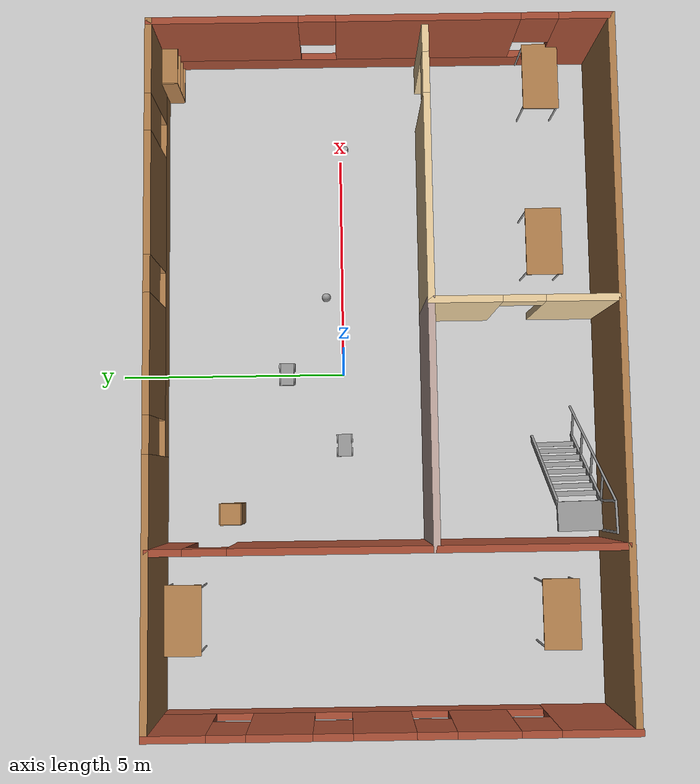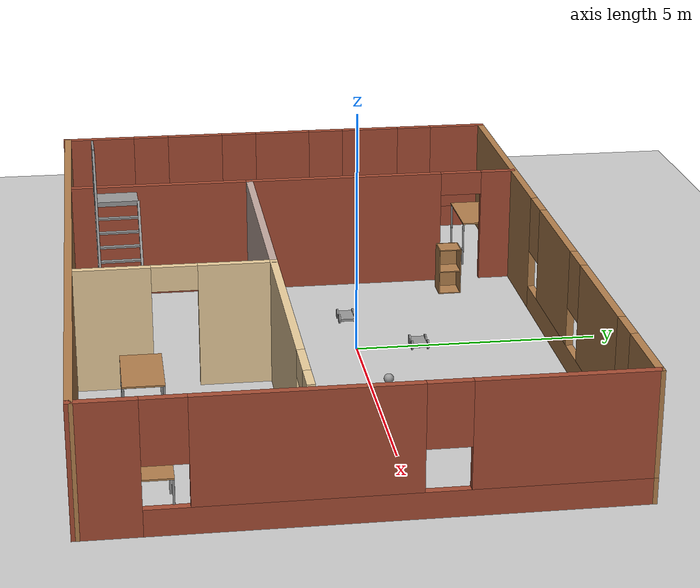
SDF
<sdf version="1.6">
 <world name="default">
  <plugin name="welcome" filename="libwelcome.so"/>
  <light name="sun" type="directional">
   <pose>0 0 10 0 -0 0</pose>
   <diffuse>0.8 0.8 0.8 1</diffuse>
   <specular>0.2 0.2 0.2 1</specular>
   <attenuation>
    <range>1000</range>
    <constant>0.9</constant>
    <linear>0.01</linear>
    <quadratic>0.001</quadratic>
   </attenuation>
   <direction>-0.5 0.1 -0.9</direction>
  </light>
  <model name="ground_plane">
   <static>1</static>
   <link name="link">
    <collision name="collision">
     <geometry><plane><normal>0 0 1</normal><size>100 100</size></plane></geometry>
     <surface>
      <contact><collide_bitmask>65535</collide_bitmask></contact>
      <friction><ode><mu>100</mu><mu2>50</mu2></ode></friction>
     </surface>
    </collision>
    <visual name="visual">
     <cast_shadows>0</cast_shadows>
     <geometry><plane><normal>0 0 1</normal><size>100 100</size></plane></geometry>
     <material>
      <script><uri>file://media/materials/scripts/gazebo.material</uri><name>Gazebo/Grey</name></script>
     </material>
    </visual>
   </link>
  </model>
  <gravity>0 0 -9.8</gravity>
  <magnetic_field>6e-06 2.3e-05 -4.2e-05</magnetic_field>
  <atmosphere type="adiabatic"/>
  <physics name="default_physics" default="0" type="ode">
   <max_step_size>0.001</max_step_size>
   <real_time_factor>1</real_time_factor>
   <real_time_update_rate>1000</real_time_update_rate>
  </physics>
  <scene><ambient>0.4 0.4 0.4 1</ambient><background>0.7 0.7 0.7 1</background><shadows>1</shadows></scene>
  <spherical_coordinates>
   <surface_model>EARTH_WGS84</surface_model>
   <latitude_deg>0</latitude_deg>
   <longitude_deg>0</longitude_deg>
   <elevation>0</elevation>
   <heading_deg>0</heading_deg>
  </spherical_coordinates>
  <model name="four_wd">
   <link name="link_0">
    <pose>-6.8e-05 0 0 0 -0 0</pose>
    <inertial>
     <mass>1</mass>
     <inertia>
      <ixx>0.166667</ixx>
      <ixy>0</ixy>
      <ixz>0</ixz>
      <iyy>0.166667</iyy>
      <iyz>0</iyz>
      <izz>0.166667</izz>
     </inertia>
    </inertial>
    <visual name="visual">
     <geometry><box><size>0.5 0.3 0.05</size></box></geometry>
     <material>
      <lighting>1</lighting>
      <script><uri>file://media/materials/scripts/gazebo.material</uri><name>Gazebo/Grey</name></script>
      <shader type="pixel"><normal_map>__default__</normal_map></shader>
      <ambient>0.3 0.3 0.3 1</ambient>
      <diffuse>0.7 0.7 0.7 1</diffuse>
      <specular>0.01 0.01 0.01 1</specular>
      <emissive>0 0 0 1</emissive>
     </material>
    </visual>
    <collision name="collision">
     <geometry><box><size>0.5 0.3 0.05</size></box></geometry>
     <surface>
      <friction>
       <ode><mu>1</mu><mu2>1</mu2><fdir1>0 0 0</fdir1><slip1>0</slip1><slip2>0</slip2></ode>
       <torsional>
        <coefficient>1</coefficient>
        <patch_radius>0</patch_radius>
        <surface_radius>0</surface_radius>
        <use_patch_radius>1</use_patch_radius>
        <ode><slip>0</slip></ode>
       </torsional>
      </friction>
      <bounce><restitution_coefficient>0</restitution_coefficient><threshold>1e+06</threshold></bounce>
      <contact>
       <collide_without_contact>0</collide_without_contact>
       <collide_without_contact_bitmask>1</collide_without_contact_bitmask>
       <collide_bitmask>1</collide_bitmask>
       <ode>
        <soft_cfm>0</soft_cfm>
        <soft_erp>0.2</soft_erp>
        <kp>1e+13</kp>
        <kd>1</kd>
        <max_vel>0.01</max_vel>
        <min_depth>0</min_depth>
       </ode>
       <bullet>
        <split_impulse>1</split_impulse>
        <split_impulse_penetration_threshold>-0.01</split_impulse_penetration_threshold>
        <soft_cfm>0</soft_cfm>
        <soft_erp>0.2</soft_erp>
        <kp>1e+13</kp>
        <kd>1</kd>
       </bullet>
      </contact>
     </surface>
    </collision>
   </link>
   <link name="link_1_clone">
    <pose>0.149932 0.16501 0 1.5707 -0 0</pose>
    <inertial>
     <mass>1</mass>
     <inertia><ixx>0.145833</ixx><ixy>0</ixy><ixz>0</ixz><iyy>0.145833</iyy><iyz>0</iyz><izz>0.125</izz></inertia>
    </inertial>
    <visual name="visual">
     <geometry><cylinder><radius>0.1</radius><length>0.03</length></cylinder></geometry>
     <material>
      <lighting>1</lighting>
      <script><uri>file://media/materials/scripts/gazebo.material</uri><name>Gazebo/Grey</name></script>
      <shader type="pixel"><normal_map>__default__</normal_map></shader>
      <ambient>0.3 0.3 0.3 1</ambient>
      <diffuse>0.7 0.7 0.7 1</diffuse>
      <specular>0.01 0.01 0.01 1</specular>
      <emissive>0 0 0 1</emissive>
     </material>
    </visual>
    <collision name="collision">
     <geometry><cylinder><radius>0.1</radius><length>0.03</length></cylinder></geometry>
     <surface>
      <friction>
       <ode><mu>1</mu><mu2>1</mu2><fdir1>0 0 0</fdir1><slip1>0</slip1><slip2>0</slip2></ode>
       <torsional>
        <coefficient>1</coefficient>
        <patch_radius>0</patch_radius>
        <surface_radius>0</surface_radius>
        <use_patch_radius>1</use_patch_radius>
        <ode><slip>0</slip></ode>
       </torsional>
      </friction>
      <bounce><restitution_coefficient>0</restitution_coefficient><threshold>1e+06</threshold></bounce>
      <contact>
       <collide_without_contact>0</collide_without_contact>
       <collide_without_contact_bitmask>1</collide_without_contact_bitmask>
       <collide_bitmask>1</collide_bitmask>
       <ode>
        <soft_cfm>0</soft_cfm>
        <soft_erp>0.2</soft_erp>
        <kp>1e+13</kp>
        <kd>1</kd>
        <max_vel>0.01</max_vel>
        <min_depth>0</min_depth>
       </ode>
       <bullet>
        <split_impulse>1</split_impulse>
        <split_impulse_penetration_threshold>-0.01</split_impulse_penetration_threshold>
        <soft_cfm>0</soft_cfm>
        <soft_erp>0.2</soft_erp>
        <kp>1e+13</kp>
        <kd>1</kd>
       </bullet>
      </contact>
     </surface>
    </collision>
   </link>
   <link name="link_1_clone_1">
    <pose>-0.150068 0.16501 0 1.5707 -0 0</pose>
    <inertial>
     <mass>1</mass>
     <inertia><ixx>0.145833</ixx><ixy>0</ixy><ixz>0</ixz><iyy>0.145833</iyy><iyz>0</iyz><izz>0.125</izz></inertia>
    </inertial>
    <visual name="visual">
     <geometry><cylinder><radius>0.1</radius><length>0.03</length></cylinder></geometry>
     <material>
      <lighting>1</lighting>
      <script><uri>file://media/materials/scripts/gazebo.material</uri><name>Gazebo/Grey</name></script>
      <shader type="pixel"><normal_map>__default__</normal_map></shader>
      <ambient>0.3 0.3 0.3 1</ambient>
      <diffuse>0.7 0.7 0.7 1</diffuse>
      <specular>0.01 0.01 0.01 1</specular>
      <emissive>0 0 0 1</emissive>
     </material>
    </visual>
    <collision name="collision">
     <geometry><cylinder><radius>0.1</radius><length>0.03</length></cylinder></geometry>
     <surface>
      <friction>
       <ode><mu>1</mu><mu2>1</mu2><fdir1>0 0 0</fdir1><slip1>0</slip1><slip2>0</slip2></ode>
       <torsional>
        <coefficient>1</coefficient>
        <patch_radius>0</patch_radius>
        <surface_radius>0</surface_radius>
        <use_patch_radius>1</use_patch_radius>
        <ode><slip>0</slip></ode>
       </torsional>
      </friction>
      <bounce><restitution_coefficient>0</restitution_coefficient><threshold>1e+06</threshold></bounce>
      <contact>
       <collide_without_contact>0</collide_without_contact>
       <collide_without_contact_bitmask>1</collide_without_contact_bitmask>
       <collide_bitmask>1</collide_bitmask>
       <ode>
        <soft_cfm>0</soft_cfm>
        <soft_erp>0.2</soft_erp>
        <kp>1e+13</kp>
        <kd>1</kd>
        <max_vel>0.01</max_vel>
        <min_depth>0</min_depth>
       </ode>
       <bullet>
        <split_impulse>1</split_impulse>
        <split_impulse_penetration_threshold>-0.01</split_impulse_penetration_threshold>
        <soft_cfm>0</soft_cfm>
        <soft_erp>0.2</soft_erp>
        <kp>1e+13</kp>
        <kd>1</kd>
       </bullet>
      </contact>
     </surface>
    </collision>
   </link>
   <link name="link_1_clone_1_clone">
    <pose>-0.150068 -0.16501 0 1.5707 -0 0</pose>
    <inertial>
     <mass>1</mass>
     <inertia><ixx>0.145833</ixx><ixy>0</ixy><ixz>0</ixz><iyy>0.145833</iyy><iyz>0</iyz><izz>0.125</izz></inertia>
    </inertial>
    <visual name="visual">
     <geometry><cylinder><radius>0.1</radius><length>0.03</length></cylinder></geometry>
     <material>
      <lighting>1</lighting>
      <script><uri>file://media/materials/scripts/gazebo.material</uri><name>Gazebo/Grey</name></script>
      <shader type="pixel"><normal_map>__default__</normal_map></shader>
      <ambient>0.3 0.3 0.3 1</ambient>
      <diffuse>0.7 0.7 0.7 1</diffuse>
      <specular>0.01 0.01 0.01 1</specular>
      <emissive>0 0 0 1</emissive>
     </material>
    </visual>
    <collision name="collision">
     <geometry><cylinder><radius>0.1</radius><length>0.03</length></cylinder></geometry>
     <surface>
      <friction>
       <ode><mu>1</mu><mu2>1</mu2><fdir1>0 0 0</fdir1><slip1>0</slip1><slip2>0</slip2></ode>
       <torsional>
        <coefficient>1</coefficient>
        <patch_radius>0</patch_radius>
        <surface_radius>0</surface_radius>
        <use_patch_radius>1</use_patch_radius>
        <ode><slip>0</slip></ode>
       </torsional>
      </friction>
      <bounce><restitution_coefficient>0</restitution_coefficient><threshold>1e+06</threshold></bounce>
      <contact>
       <collide_without_contact>0</collide_without_contact>
       <collide_without_contact_bitmask>1</collide_without_contact_bitmask>
       <collide_bitmask>1</collide_bitmask>
       <ode>
        <soft_cfm>0</soft_cfm>
        <soft_erp>0.2</soft_erp>
        <kp>1e+13</kp>
        <kd>1</kd>
        <max_vel>0.01</max_vel>
        <min_depth>0</min_depth>
       </ode>
       <bullet>
        <split_impulse>1</split_impulse>
        <split_impulse_penetration_threshold>-0.01</split_impulse_penetration_threshold>
        <soft_cfm>0</soft_cfm>
        <soft_erp>0.2</soft_erp>
        <kp>1e+13</kp>
        <kd>1</kd>
       </bullet>
      </contact>
     </surface>
    </collision>
   </link>
   <link name="link_1_clone_1_clone_0">
    <pose>0.149932 -0.16501 0 1.5707 -0 0</pose>
    <inertial>
     <mass>1</mass>
     <inertia><ixx>0.145833</ixx><ixy>0</ixy><ixz>0</ixz><iyy>0.145833</iyy><iyz>0</iyz><izz>0.125</izz></inertia>
    </inertial>
    <visual name="visual">
     <geometry><cylinder><radius>0.1</radius><length>0.03</length></cylinder></geometry>
     <material>
      <lighting>1</lighting>
      <script><uri>file://media/materials/scripts/gazebo.material</uri><name>Gazebo/Grey</name></script>
      <shader type="pixel"><normal_map>__default__</normal_map></shader>
      <ambient>0.3 0.3 0.3 1</ambient>
      <diffuse>0.7 0.7 0.7 1</diffuse>
      <specular>0.01 0.01 0.01 1</specular>
      <emissive>0 0 0 1</emissive>
     </material>
    </visual>
    <collision name="collision">
     <geometry><cylinder><radius>0.1</radius><length>0.03</length></cylinder></geometry>
     <surface>
      <friction>
       <ode><mu>1</mu><mu2>1</mu2><fdir1>0 0 0</fdir1><slip1>0</slip1><slip2>0</slip2></ode>
       <torsional>
        <coefficient>1</coefficient>
        <patch_radius>0</patch_radius>
        <surface_radius>0</surface_radius>
        <use_patch_radius>1</use_patch_radius>
        <ode><slip>0</slip></ode>
       </torsional>
      </friction>
      <bounce><restitution_coefficient>0</restitution_coefficient><threshold>1e+06</threshold></bounce>
      <contact>
       <collide_without_contact>0</collide_without_contact>
       <collide_without_contact_bitmask>1</collide_without_contact_bitmask>
       <collide_bitmask>1</collide_bitmask>
       <ode>
        <soft_cfm>0</soft_cfm>
        <soft_erp>0.2</soft_erp>
        <kp>1e+13</kp>
        <kd>1</kd>
        <max_vel>0.01</max_vel>
        <min_depth>0</min_depth>
       </ode>
       <bullet>
        <split_impulse>1</split_impulse>
        <split_impulse_penetration_threshold>-0.01</split_impulse_penetration_threshold>
        <soft_cfm>0</soft_cfm>
        <soft_erp>0.2</soft_erp>
        <kp>1e+13</kp>
        <kd>1</kd>
       </bullet>
      </contact>
     </surface>
    </collision>
   </link>
   <joint name="link_0_JOINT_3" type="revolute">
    <parent>link_0</parent>
    <child>link_1_clone</child>
    <axis>
     <xyz>1 0 0</xyz>
     <use_parent_model_frame>0</use_parent_model_frame>
     <limit>
      <lower>-1.79769e+308</lower>
      <upper>1.79769e+308</upper>
      <effort>-1</effort>
      <velocity>-1</velocity>
     </limit>
     <dynamics>
      <spring_reference>0</spring_reference>
      <spring_stiffness>0</spring_stiffness>
      <damping>0</damping>
     </dynamics>
    </axis>
    <physics>
     <ode><limit><cfm>0</cfm><erp>0.2</erp></limit><suspension><cfm>0</cfm><erp>0.2</erp></suspension></ode>
    </physics>
   </joint>
   <joint name="link_0_JOINT_4" type="revolute">
    <parent>link_0</parent>
    <child>link_1_clone_1</child>
    <axis>
     <xyz>0 0 1</xyz>
     <use_parent_model_frame>0</use_parent_model_frame>
     <limit>
      <lower>-1.79769e+308</lower>
      <upper>1.79769e+308</upper>
      <effort>-1</effort>
      <velocity>-1</velocity>
     </limit>
     <dynamics>
      <spring_reference>0</spring_reference>
      <spring_stiffness>0</spring_stiffness>
      <damping>0</damping>
     </dynamics>
    </axis>
    <physics>
     <ode><limit><cfm>0</cfm><erp>0.2</erp></limit><suspension><cfm>0</cfm><erp>0.2</erp></suspension></ode>
    </physics>
   </joint>
   <joint name="link_0_JOINT_5" type="revolute">
    <parent>link_0</parent>
    <child>link_1_clone_1_clone_0</child>
    <axis>
     <xyz>0 0 1</xyz>
     <use_parent_model_frame>0</use_parent_model_frame>
     <limit>
      <lower>-1.79769e+308</lower>
      <upper>1.79769e+308</upper>
      <effort>-1</effort>
      <velocity>-1</velocity>
     </limit>
     <dynamics>
      <spring_reference>0</spring_reference>
      <spring_stiffness>0</spring_stiffness>
      <damping>0</damping>
     </dynamics>
    </axis>
    <physics>
     <ode><limit><cfm>0</cfm><erp>0.2</erp></limit><suspension><cfm>0</cfm><erp>0.2</erp></suspension></ode>
    </physics>
   </joint>
   <joint name="link_0_JOINT_6" type="revolute">
    <parent>link_0</parent>
    <child>link_1_clone_1_clone</child>
    <axis>
     <xyz>0 0 1</xyz>
     <use_parent_model_frame>0</use_parent_model_frame>
     <limit>
      <lower>-1.79769e+308</lower>
      <upper>1.79769e+308</upper>
      <effort>-1</effort>
      <velocity>-1</velocity>
     </limit>
     <dynamics>
      <spring_reference>0</spring_reference>
      <spring_stiffness>0</spring_stiffness>
      <damping>0</damping>
     </dynamics>
    </axis>
    <physics>
     <ode><limit><cfm>0</cfm><erp>0.2</erp></limit><suspension><cfm>0</cfm><erp>0.2</erp></suspension></ode>
    </physics>
   </joint>
   <static>0</static>
   <pose>-1.5932 0.001925 0.100001 -4e-06 1e-06 0.01208</pose>
  </model>
  <model name="project_structure">
   <pose>-0.032624 -0.85735 0 0 -0 0</pose>
   <link name="Wall_15">
    <collision name="Wall_15_Collision">
     <geometry><box><size>14.9541 0.15 2.5</size></box></geometry>
     <pose>0 0 1.25 0 -0 0</pose>
    </collision>
    <visual name="Wall_15_Visual">
     <pose>0 0 1.25 0 -0 0</pose>
     <geometry><box><size>14.9541 0.15 2.5</size></box></geometry>
     <material>
      <script><uri>file://media/materials/scripts/gazebo.material</uri><name>Gazebo/Wood</name></script>
      <ambient>0.921569 0.807843 0.615686 1</ambient>
     </material>
     <meta><layer>0</layer></meta>
    </visual>
    <pose>0.011442 -4.91344 0 0 0 -0.003107</pose>
   </link>
   <link name="Wall_21">
    <pose>-7.41356 0.011558 0 0 -0 1.5708</pose>
    <visual name="Wall_21_Visual_0">
     <pose>-4.18397 0 1.25 0 -0 0</pose>
     <geometry><box><size>1.63206 0.15 2.5</size></box></geometry>
     <material>
      <script><uri>file://media/materials/scripts/gazebo.material</uri><name>Gazebo/Bricks</name></script>
      <ambient>0.760784 0.662745 0.627451 1</ambient>
     </material>
     <meta><layer>0</layer></meta>
    </visual>
    <collision name="Wall_21_Collision_0">
     <geometry><box><size>1.63206 0.15 2.5</size></box></geometry>
     <pose>-4.18397 0 1.25 0 -0 0</pose>
    </collision>
    <visual name="Wall_21_Visual_1">
     <pose>0.816032 0 0.25 0 -0 0</pose>
     <geometry><box><size>8.36794 0.15 0.5</size></box></geometry>
     <material>
      <script><uri>file://media/materials/scripts/gazebo.material</uri><name>Gazebo/Bricks</name></script>
      <ambient>0.760784 0.662745 0.627451 1</ambient>
     </material>
     <meta><layer>0</layer></meta>
    </visual>
    <collision name="Wall_21_Collision_1">
     <geometry><box><size>8.36794 0.15 0.5</size></box></geometry>
     <pose>0.816032 0 0.25 0 -0 0</pose>
    </collision>
    <visual name="Wall_21_Visual_2">
     <pose>-1.93374 0 1.5 0 -0 0</pose>
     <geometry><box><size>1.26839 0.15 2</size></box></geometry>
     <material>
      <script><uri>file://media/materials/scripts/gazebo.material</uri><name>Gazebo/Bricks</name></script>
      <ambient>0.760784 0.662745 0.627451 1</ambient>
     </material>
     <meta><layer>0</layer></meta>
    </visual>
    <collision name="Wall_21_Collision_2">
     <geometry><box><size>1.26839 0.15 2</size></box></geometry>
     <pose>-1.93374 0 1.5 0 -0 0</pose>
    </collision>
    <visual name="Wall_21_Visual_3">
     <pose>0.134648 0 1.5 0 -0 0</pose>
     <geometry><box><size>1.26839 0.15 2</size></box></geometry>
     <material>
      <script><uri>file://media/materials/scripts/gazebo.material</uri><name>Gazebo/Bricks</name></script>
      <ambient>0.760784 0.662745 0.627451 1</ambient>
     </material>
     <meta><layer>0</layer></meta>
    </visual>
    <collision name="Wall_21_Collision_3">
     <geometry><box><size>1.26839 0.15 2</size></box></geometry>
     <pose>0.134648 0 1.5 0 -0 0</pose>
    </collision>
    <visual name="Wall_21_Visual_4">
     <pose>2.23346 0 1.5 0 -0 0</pose>
     <geometry><box><size>1.32923 0.15 2</size></box></geometry>
     <material>
      <script><uri>file://media/materials/scripts/gazebo.material</uri><name>Gazebo/Bricks</name></script>
      <ambient>0.760784 0.662745 0.627451 1</ambient>
     </material>
     <meta><layer>0</layer></meta>
    </visual>
    <collision name="Wall_21_Collision_4">
     <geometry><box><size>1.32923 0.15 2</size></box></geometry>
     <pose>2.23346 0 1.5 0 -0 0</pose>
    </collision>
    <visual name="Wall_21_Visual_5">
     <pose>4.34903 0 1.5 0 -0 0</pose>
     <geometry><box><size>1.30193 0.15 2</size></box></geometry>
     <material>
      <script><uri>file://media/materials/scripts/gazebo.material</uri><name>Gazebo/Bricks</name></script>
      <ambient>0.760784 0.662745 0.627451 1</ambient>
     </material>
     <meta><layer>0</layer></meta>
    </visual>
    <collision name="Wall_21_Collision_5">
     <geometry><box><size>1.30193 0.15 2</size></box></geometry>
     <pose>4.34903 0 1.5 0 -0 0</pose>
    </collision>
    <visual name="Wall_21_Visual_6">
     <pose>-2.96794 0 1.9 0 -0 0</pose>
     <geometry><box><size>0.8 0.15 1.2</size></box></geometry>
     <material>
      <script><uri>file://media/materials/scripts/gazebo.material</uri><name>Gazebo/Bricks</name></script>
      <ambient>0.760784 0.662745 0.627451 1</ambient>
     </material>
     <meta><layer>0</layer></meta>
    </visual>
    <collision name="Wall_21_Collision_6">
     <geometry><box><size>0.8 0.15 1.2</size></box></geometry>
     <pose>-2.96794 0 1.9 0 -0 0</pose>
    </collision>
    <visual name="Wall_21_Visual_7">
     <pose>-0.899547 0 1.9 0 -0 0</pose>
     <geometry><box><size>0.8 0.15 1.2</size></box></geometry>
     <material>
      <script><uri>file://media/materials/scripts/gazebo.material</uri><name>Gazebo/Bricks</name></script>
      <ambient>0.760784 0.662745 0.627451 1</ambient>
     </material>
     <meta><layer>0</layer></meta>
    </visual>
    <collision name="Wall_21_Collision_7">
     <geometry><box><size>0.8 0.15 1.2</size></box></geometry>
     <pose>-0.899547 0 1.9 0 -0 0</pose>
    </collision>
    <visual name="Wall_21_Visual_8">
     <pose>1.16884 0 1.9 0 -0 0</pose>
     <geometry><box><size>0.8 0.15 1.2</size></box></geometry>
     <material>
      <script><uri>file://media/materials/scripts/gazebo.material</uri><name>Gazebo/Bricks</name></script>
      <ambient>0.760784 0.662745 0.627451 1</ambient>
     </material>
     <meta><layer>0</layer></meta>
    </visual>
    <collision name="Wall_21_Collision_8">
     <geometry><box><size>0.8 0.15 1.2</size></box></geometry>
     <pose>1.16884 0 1.9 0 -0 0</pose>
    </collision>
    <visual name="Wall_21_Visual_9">
     <pose>3.29807 0 1.9 0 -0 0</pose>
     <geometry><box><size>0.8 0.15 1.2</size></box></geometry>
     <material>
      <script><uri>file://media/materials/scripts/gazebo.material</uri><name>Gazebo/Bricks</name></script>
      <ambient>0.760784 0.662745 0.627451 1</ambient>
     </material>
     <meta><layer>0</layer></meta>
    </visual>
    <collision name="Wall_21_Collision_9">
     <geometry><box><size>0.8 0.15 1.2</size></box></geometry>
     <pose>3.29807 0 1.9 0 -0 0</pose>
    </collision>
   </link>
   <link name="Wall_23">
    <pose>7.41344 -0.011442 0 0 -0 1.5708</pose>
    <visual name="Wall_23_Visual_0">
     <pose>-4.4006 0 1.25 0 -0 0</pose>
     <geometry><box><size>1.1988 0.15 2.5</size></box></geometry>
     <material>
      <script><uri>file://media/materials/scripts/gazebo.material</uri><name>Gazebo/Bricks</name></script>
      <ambient>0.921569 0.807843 0.615686 1</ambient>
     </material>
     <meta><layer>0</layer></meta>
    </visual>
    <collision name="Wall_23_Collision_0">
     <geometry><box><size>1.1988 0.15 2.5</size></box></geometry>
     <pose>-4.4006 0 1.25 0 -0 0</pose>
    </collision>
    <visual name="Wall_23_Visual_1">
     <pose>0.5994 0 0.25 0 -0 0</pose>
     <geometry><box><size>8.8012 0.15 0.5</size></box></geometry>
     <material>
      <script><uri>file://media/materials/scripts/gazebo.material</uri><name>Gazebo/Bricks</name></script>
      <ambient>0.921569 0.807843 0.615686 1</ambient>
     </material>
     <meta><layer>0</layer></meta>
    </visual>
    <collision name="Wall_23_Collision_1">
     <geometry><box><size>8.8012 0.15 0.5</size></box></geometry>
     <pose>0.5994 0 0.25 0 -0 0</pose>
    </collision>
    <visual name="Wall_23_Visual_2">
     <pose>-1.02863 0 1.5 0 -0 0</pose>
     <geometry><box><size>3.94513 0.15 2</size></box></geometry>
     <material>
      <script><uri>file://media/materials/scripts/gazebo.material</uri><name>Gazebo/Bricks</name></script>
      <ambient>0.921569 0.807843 0.615686 1</ambient>
     </material>
     <meta><layer>0</layer></meta>
    </visual>
    <collision name="Wall_23_Collision_2">
     <geometry><box><size>3.94513 0.15 2</size></box></geometry>
     <pose>-1.02863 0 1.5 0 -0 0</pose>
    </collision>
    <visual name="Wall_23_Visual_3">
     <pose>3.37196 0 1.5 0 -0 0</pose>
     <geometry><box><size>3.25607 0.15 2</size></box></geometry>
     <material>
      <script><uri>file://media/materials/scripts/gazebo.material</uri><name>Gazebo/Bricks</name></script>
      <ambient>0.921569 0.807843 0.615686 1</ambient>
     </material>
     <meta><layer>0</layer></meta>
    </visual>
    <collision name="Wall_23_Collision_3">
     <geometry><box><size>3.25607 0.15 2</size></box></geometry>
     <pose>3.37196 0 1.5 0 -0 0</pose>
    </collision>
    <visual name="Wall_23_Visual_4">
     <pose>-3.4012 0 1.9 0 -0 0</pose>
     <geometry><box><size>0.8 0.15 1.2</size></box></geometry>
     <material>
      <script><uri>file://media/materials/scripts/gazebo.material</uri><name>Gazebo/Bricks</name></script>
      <ambient>0.921569 0.807843 0.615686 1</ambient>
     </material>
     <meta><layer>0</layer></meta>
    </visual>
    <collision name="Wall_23_Collision_4">
     <geometry><box><size>0.8 0.15 1.2</size></box></geometry>
     <pose>-3.4012 0 1.9 0 -0 0</pose>
    </collision>
    <visual name="Wall_23_Visual_5">
     <pose>1.34393 0 1.9 0 -0 0</pose>
     <geometry><box><size>0.8 0.15 1.2</size></box></geometry>
     <material>
      <script><uri>file://media/materials/scripts/gazebo.material</uri><name>Gazebo/Bricks</name></script>
      <ambient>0.921569 0.807843 0.615686 1</ambient>
     </material>
     <meta><layer>0</layer></meta>
    </visual>
    <collision name="Wall_23_Collision_5">
     <geometry><box><size>0.8 0.15 1.2</size></box></geometry>
     <pose>1.34393 0 1.9 0 -0 0</pose>
    </collision>
   </link>
   <link name="Wall_25">
    <pose>-5.8e-05 4.92506 0 0 0 -0.001551</pose>
    <visual name="Wall_25_Visual_0">
     <pose>-4.62864 0 1.25 0 -0 0</pose>
     <geometry><box><size>5.71975 0.15 2.5</size></box></geometry>
     <material>
      <script><uri>file://media/materials/scripts/gazebo.material</uri><name>Gazebo/Wood</name></script>
      <ambient>0.760784 0.662745 0.627451 1</ambient>
     </material>
     <meta><layer>0</layer></meta>
    </visual>
    <collision name="Wall_25_Collision_0">
     <geometry><box><size>5.71975 0.15 2.5</size></box></geometry>
     <pose>-4.62864 0 1.25 0 -0 0</pose>
    </collision>
    <visual name="Wall_25_Visual_1">
     <pose>2.85987 0 0.25 0 -0 0</pose>
     <geometry><box><size>9.25727 0.15 0.5</size></box></geometry>
     <material>
      <script><uri>file://media/materials/scripts/gazebo.material</uri><name>Gazebo/Wood</name></script>
      <ambient>0.760784 0.662745 0.627451 1</ambient>
     </material>
     <meta><layer>0</layer></meta>
    </visual>
    <collision name="Wall_25_Collision_1">
     <geometry><box><size>9.25727 0.15 0.5</size></box></geometry>
     <pose>2.85987 0 0.25 0 -0 0</pose>
    </collision>
    <visual name="Wall_25_Visual_2">
     <pose>0.300724 0 1.5 0 -0 0</pose>
     <geometry><box><size>2.53897 0.15 2</size></box></geometry>
     <material>
      <script><uri>file://media/materials/scripts/gazebo.material</uri><name>Gazebo/Wood</name></script>
      <ambient>0.760784 0.662745 0.627451 1</ambient>
     </material>
     <meta><layer>0</layer></meta>
    </visual>
    <collision name="Wall_25_Collision_2">
     <geometry><box><size>2.53897 0.15 2</size></box></geometry>
     <pose>0.300724 0 1.5 0 -0 0</pose>
    </collision>
    <visual name="Wall_25_Visual_3">
     <pose>3.69995 0 1.5 0 -0 0</pose>
     <geometry><box><size>2.65947 0.15 2</size></box></geometry>
     <material>
      <script><uri>file://media/materials/scripts/gazebo.material</uri><name>Gazebo/Wood</name></script>
      <ambient>0.760784 0.662745 0.627451 1</ambient>
     </material>
     <meta><layer>0</layer></meta>
    </visual>
    <collision name="Wall_25_Collision_3">
     <geometry><box><size>2.65947 0.15 2</size></box></geometry>
     <pose>3.69995 0 1.5 0 -0 0</pose>
    </collision>
    <visual name="Wall_25_Visual_4">
     <pose>6.65909 0 1.5 0 -0 0</pose>
     <geometry><box><size>1.65883 0.15 2</size></box></geometry>
     <material>
      <script><uri>file://media/materials/scripts/gazebo.material</uri><name>Gazebo/Wood</name></script>
      <ambient>0.760784 0.662745 0.627451 1</ambient>
     </material>
     <meta><layer>0</layer></meta>
    </visual>
    <collision name="Wall_25_Collision_4">
     <geometry><box><size>1.65883 0.15 2</size></box></geometry>
     <pose>6.65909 0 1.5 0 -0 0</pose>
    </collision>
    <visual name="Wall_25_Visual_5">
     <pose>-1.36876 0 1.9 0 -0 0</pose>
     <geometry><box><size>0.8 0.15 1.2</size></box></geometry>
     <material>
      <script><uri>file://media/materials/scripts/gazebo.material</uri><name>Gazebo/Wood</name></script>
      <ambient>0.760784 0.662745 0.627451 1</ambient>
     </material>
     <meta><layer>0</layer></meta>
    </visual>
    <collision name="Wall_25_Collision_5">
     <geometry><box><size>0.8 0.15 1.2</size></box></geometry>
     <pose>-1.36876 0 1.9 0 -0 0</pose>
    </collision>
    <visual name="Wall_25_Visual_6">
     <pose>1.97021 0 1.9 0 -0 0</pose>
     <geometry><box><size>0.8 0.15 1.2</size></box></geometry>
     <material>
      <script><uri>file://media/materials/scripts/gazebo.material</uri><name>Gazebo/Wood</name></script>
      <ambient>0.760784 0.662745 0.627451 1</ambient>
     </material>
     <meta><layer>0</layer></meta>
    </visual>
    <collision name="Wall_25_Collision_6">
     <geometry><box><size>0.8 0.15 1.2</size></box></geometry>
     <pose>1.97021 0 1.9 0 -0 0</pose>
    </collision>
    <visual name="Wall_25_Visual_7">
     <pose>5.42968 0 1.9 0 -0 0</pose>
     <geometry><box><size>0.8 0.15 1.2</size></box></geometry>
     <material>
      <script><uri>file://media/materials/scripts/gazebo.material</uri><name>Gazebo/Wood</name></script>
      <ambient>0.760784 0.662745 0.627451 1</ambient>
     </material>
     <meta><layer>0</layer></meta>
    </visual>
    <collision name="Wall_25_Collision_7">
     <geometry><box><size>0.8 0.15 1.2</size></box></geometry>
     <pose>5.42968 0 1.9 0 -0 0</pose>
    </collision>
   </link>
   <link name="Wall_27">
    <pose>-3.76645 1.95597 0 0 0 -1.5708</pose>
    <visual name="Wall_27_Visual_0">
     <pose>-2.61475 0 1.25 0 -0 0</pose>
     <geometry><box><size>0.770497 0.15 2.5</size></box></geometry>
     <material>
      <script><uri>file://media/materials/scripts/gazebo.material</uri><name>Gazebo/Bricks</name></script>
      <ambient>0.760784 0.662745 0.627451 1</ambient>
     </material>
     <meta><layer>0</layer></meta>
    </visual>
    <collision name="Wall_27_Collision_0">
     <geometry><box><size>0.770497 0.15 2.5</size></box></geometry>
     <pose>-2.61475 0 1.25 0 -0 0</pose>
    </collision>
    <visual name="Wall_27_Visual_1">
     <pose>0.835249 0 1.25 0 -0 0</pose>
     <geometry><box><size>4.3295 0.15 2.5</size></box></geometry>
     <material>
      <script><uri>file://media/materials/scripts/gazebo.material</uri><name>Gazebo/Bricks</name></script>
      <ambient>0.760784 0.662745 0.627451 1</ambient>
     </material>
     <meta><layer>0</layer></meta>
    </visual>
    <collision name="Wall_27_Collision_1">
     <geometry><box><size>4.3295 0.15 2.5</size></box></geometry>
     <pose>0.835249 0 1.25 0 -0 0</pose>
    </collision>
    <visual name="Wall_27_Visual_2">
     <pose>-1.7795 0 2.25 0 -0 0</pose>
     <geometry><box><size>0.9 0.15 0.5</size></box></geometry>
     <material>
      <script><uri>file://media/materials/scripts/gazebo.material</uri><name>Gazebo/Bricks</name></script>
      <ambient>0.760784 0.662745 0.627451 1</ambient>
     </material>
     <meta><layer>0</layer></meta>
    </visual>
    <collision name="Wall_27_Collision_2">
     <geometry><box><size>0.9 0.15 0.5</size></box></geometry>
     <pose>-1.7795 0 2.25 0 -0 0</pose>
    </collision>
   </link>
   <link name="Wall_28">
    <collision name="Wall_28_Collision">
     <geometry><box><size>5.25 0.15 2.5</size></box></geometry>
     <pose>0 0 1.25 0 -0 0</pose>
    </collision>
    <visual name="Wall_28_Visual">
     <pose>0 0 1.25 0 -0 0</pose>
     <geometry><box><size>5.25 0.15 2.5</size></box></geometry>
     <material>
      <script><uri>file://media/materials/scripts/gazebo.material</uri><name>Gazebo/Grey</name></script>
      <ambient>0.760784 0.662745 0.627451 1</ambient>
     </material>
     <meta><layer>0</layer></meta>
    </visual>
    <pose>-1.21644 -0.969031 0 0 -0 0</pose>
   </link>
   <link name="Wall_29">
    <pose>1.33356 -2.89403 0 0 0 -1.5708</pose>
    <visual name="Wall_29_Visual_0">
     <pose>-1.22424 0 1.25 0 -0 0</pose>
     <geometry><box><size>1.55151 0.15 2.5</size></box></geometry>
     <material>
      <script><uri>file://media/materials/scripts/gazebo.material</uri><name>Gazebo/Grey</name></script>
      <ambient>0.921569 0.807843 0.615686 1</ambient>
     </material>
     <meta><layer>0</layer></meta>
    </visual>
    <collision name="Wall_29_Collision_0">
     <geometry><box><size>1.55151 0.15 2.5</size></box></geometry>
     <pose>-1.22424 0 1.25 0 -0 0</pose>
    </collision>
    <visual name="Wall_29_Visual_1">
     <pose>1.22576 0 1.25 0 -0 0</pose>
     <geometry><box><size>1.54849 0.15 2.5</size></box></geometry>
     <material>
      <script><uri>file://media/materials/scripts/gazebo.material</uri><name>Gazebo/Grey</name></script>
      <ambient>0.921569 0.807843 0.615686 1</ambient>
     </material>
     <meta><layer>0</layer></meta>
    </visual>
    <collision name="Wall_29_Collision_1">
     <geometry><box><size>1.54849 0.15 2.5</size></box></geometry>
     <pose>1.22576 0 1.25 0 -0 0</pose>
    </collision>
    <visual name="Wall_29_Visual_2">
     <pose>0.001512 0 2.25 0 -0 0</pose>
     <geometry><box><size>0.9 0.15 0.5</size></box></geometry>
     <material>
      <script><uri>file://media/materials/scripts/gazebo.material</uri><name>Gazebo/Grey</name></script>
      <ambient>0.921569 0.807843 0.615686 1</ambient>
     </material>
     <meta><layer>0</layer></meta>
    </visual>
    <collision name="Wall_29_Collision_2">
     <geometry><box><size>0.9 0.15 0.5</size></box></geometry>
     <pose>0.001512 0 2.25 0 -0 0</pose>
    </collision>
   </link>
   <link name="Wall_31">
    <pose>4.25855 -0.969031 0 0 -0 0</pose>
    <visual name="Wall_31_Visual_0">
     <pose>-0.749855 0 1.25 0 -0 0</pose>
     <geometry><box><size>4.50029 0.15 2.5</size></box></geometry>
     <material>
      <script><uri>file://media/materials/scripts/gazebo.material</uri><name>Gazebo/Grey</name></script>
      <ambient>0.921569 0.807843 0.615686 1</ambient>
     </material>
     <meta><layer>0</layer></meta>
    </visual>
    <collision name="Wall_31_Collision_0">
     <geometry><box><size>4.50029 0.15 2.5</size></box></geometry>
     <pose>-0.749855 0 1.25 0 -0 0</pose>
    </collision>
    <visual name="Wall_31_Visual_1">
     <pose>2.70015 0 1.25 0 -0 0</pose>
     <geometry><box><size>0.599711 0.15 2.5</size></box></geometry>
     <material>
      <script><uri>file://media/materials/scripts/gazebo.material</uri><name>Gazebo/Grey</name></script>
      <ambient>0.921569 0.807843 0.615686 1</ambient>
     </material>
     <meta><layer>0</layer></meta>
    </visual>
    <collision name="Wall_31_Collision_1">
     <geometry><box><size>0.599711 0.15 2.5</size></box></geometry>
     <pose>2.70015 0 1.25 0 -0 0</pose>
    </collision>
    <visual name="Wall_31_Visual_2">
     <pose>1.95029 0 2.25 0 -0 0</pose>
     <geometry><box><size>0.9 0.15 0.5</size></box></geometry>
     <material>
      <script><uri>file://media/materials/scripts/gazebo.material</uri><name>Gazebo/Grey</name></script>
      <ambient>0.921569 0.807843 0.615686 1</ambient>
     </material>
     <meta><layer>0</layer></meta>
    </visual>
    <collision name="Wall_31_Collision_2">
     <geometry><box><size>0.9 0.15 0.5</size></box></geometry>
     <pose>1.95029 0 2.25 0 -0 0</pose>
    </collision>
   </link>
   <link name="Wall_33">
    <collision name="Wall_33_Collision">
     <geometry><box><size>4 0.15 2.5</size></box></geometry>
     <pose>0 0 1.25 0 -0 0</pose>
    </collision>
    <visual name="Wall_33_Visual">
     <pose>0 0 1.25 0 -0 0</pose>
     <geometry><box><size>4 0.15 2.5</size></box></geometry>
     <material>
      <script><uri>file://media/materials/scripts/gazebo.material</uri><name>Gazebo/Bricks</name></script>
      <ambient>0.760784 0.662745 0.627451 1</ambient>
     </material>
     <meta><layer>0</layer></meta>
    </visual>
    <pose>-3.76645 -2.89403 0 0 0 -1.5708</pose>
   </link>
   <static>1</static>
  </model>
  <model name="four_wd_0">
   <link name="link_0">
    <pose>-6.8e-05 0 0 0 -0 0</pose>
    <inertial>
     <mass>1</mass>
     <inertia>
      <ixx>0.166667</ixx>
      <ixy>0</ixy>
      <ixz>0</ixz>
      <iyy>0.166667</iyy>
      <iyz>0</iyz>
      <izz>0.166667</izz>
     </inertia>
    </inertial>
    <visual name="visual">
     <geometry><box><size>0.5 0.3 0.05</size></box></geometry>
     <material>
      <lighting>1</lighting>
      <script><uri>file://media/materials/scripts/gazebo.material</uri><name>Gazebo/Grey</name></script>
      <shader type="pixel"><normal_map>__default__</normal_map></shader>
      <ambient>0.3 0.3 0.3 1</ambient>
      <diffuse>0.7 0.7 0.7 1</diffuse>
      <specular>0.01 0.01 0.01 1</specular>
      <emissive>0 0 0 1</emissive>
     </material>
    </visual>
    <collision name="collision">
     <geometry><box><size>0.5 0.3 0.05</size></box></geometry>
     <surface>
      <friction>
       <ode><mu>1</mu><mu2>1</mu2><fdir1>0 0 0</fdir1><slip1>0</slip1><slip2>0</slip2></ode>
       <torsional>
        <coefficient>1</coefficient>
        <patch_radius>0</patch_radius>
        <surface_radius>0</surface_radius>
        <use_patch_radius>1</use_patch_radius>
        <ode><slip>0</slip></ode>
       </torsional>
      </friction>
      <bounce><restitution_coefficient>0</restitution_coefficient><threshold>1e+06</threshold></bounce>
      <contact>
       <collide_without_contact>0</collide_without_contact>
       <collide_without_contact_bitmask>1</collide_without_contact_bitmask>
       <collide_bitmask>1</collide_bitmask>
       <ode>
        <soft_cfm>0</soft_cfm>
        <soft_erp>0.2</soft_erp>
        <kp>1e+13</kp>
        <kd>1</kd>
        <max_vel>0.01</max_vel>
        <min_depth>0</min_depth>
       </ode>
       <bullet>
        <split_impulse>1</split_impulse>
        <split_impulse_penetration_threshold>-0.01</split_impulse_penetration_threshold>
        <soft_cfm>0</soft_cfm>
        <soft_erp>0.2</soft_erp>
        <kp>1e+13</kp>
        <kd>1</kd>
       </bullet>
      </contact>
     </surface>
    </collision>
   </link>
   <link name="link_1_clone">
    <pose>0.149932 0.16501 0 1.5707 -0 0</pose>
    <inertial>
     <mass>1</mass>
     <inertia><ixx>0.145833</ixx><ixy>0</ixy><ixz>0</ixz><iyy>0.145833</iyy><iyz>0</iyz><izz>0.125</izz></inertia>
    </inertial>
    <visual name="visual">
     <geometry><cylinder><radius>0.1</radius><length>0.03</length></cylinder></geometry>
     <material>
      <lighting>1</lighting>
      <script><uri>file://media/materials/scripts/gazebo.material</uri><name>Gazebo/Grey</name></script>
      <shader type="pixel"><normal_map>__default__</normal_map></shader>
      <ambient>0.3 0.3 0.3 1</ambient>
      <diffuse>0.7 0.7 0.7 1</diffuse>
      <specular>0.01 0.01 0.01 1</specular>
      <emissive>0 0 0 1</emissive>
     </material>
    </visual>
    <collision name="collision">
     <geometry><cylinder><radius>0.1</radius><length>0.03</length></cylinder></geometry>
     <surface>
      <friction>
       <ode><mu>1</mu><mu2>1</mu2><fdir1>0 0 0</fdir1><slip1>0</slip1><slip2>0</slip2></ode>
       <torsional>
        <coefficient>1</coefficient>
        <patch_radius>0</patch_radius>
        <surface_radius>0</surface_radius>
        <use_patch_radius>1</use_patch_radius>
        <ode><slip>0</slip></ode>
       </torsional>
      </friction>
      <bounce><restitution_coefficient>0</restitution_coefficient><threshold>1e+06</threshold></bounce>
      <contact>
       <collide_without_contact>0</collide_without_contact>
       <collide_without_contact_bitmask>1</collide_without_contact_bitmask>
       <collide_bitmask>1</collide_bitmask>
       <ode>
        <soft_cfm>0</soft_cfm>
        <soft_erp>0.2</soft_erp>
        <kp>1e+13</kp>
        <kd>1</kd>
        <max_vel>0.01</max_vel>
        <min_depth>0</min_depth>
       </ode>
       <bullet>
        <split_impulse>1</split_impulse>
        <split_impulse_penetration_threshold>-0.01</split_impulse_penetration_threshold>
        <soft_cfm>0</soft_cfm>
        <soft_erp>0.2</soft_erp>
        <kp>1e+13</kp>
        <kd>1</kd>
       </bullet>
      </contact>
     </surface>
    </collision>
   </link>
   <link name="link_1_clone_1">
    <pose>-0.150068 0.16501 0 1.5707 -0 0</pose>
    <inertial>
     <mass>1</mass>
     <inertia><ixx>0.145833</ixx><ixy>0</ixy><ixz>0</ixz><iyy>0.145833</iyy><iyz>0</iyz><izz>0.125</izz></inertia>
    </inertial>
    <visual name="visual">
     <geometry><cylinder><radius>0.1</radius><length>0.03</length></cylinder></geometry>
     <material>
      <lighting>1</lighting>
      <script><uri>file://media/materials/scripts/gazebo.material</uri><name>Gazebo/Grey</name></script>
      <shader type="pixel"><normal_map>__default__</normal_map></shader>
      <ambient>0.3 0.3 0.3 1</ambient>
      <diffuse>0.7 0.7 0.7 1</diffuse>
      <specular>0.01 0.01 0.01 1</specular>
      <emissive>0 0 0 1</emissive>
     </material>
    </visual>
    <collision name="collision">
     <geometry><cylinder><radius>0.1</radius><length>0.03</length></cylinder></geometry>
     <surface>
      <friction>
       <ode><mu>1</mu><mu2>1</mu2><fdir1>0 0 0</fdir1><slip1>0</slip1><slip2>0</slip2></ode>
       <torsional>
        <coefficient>1</coefficient>
        <patch_radius>0</patch_radius>
        <surface_radius>0</surface_radius>
        <use_patch_radius>1</use_patch_radius>
        <ode><slip>0</slip></ode>
       </torsional>
      </friction>
      <bounce><restitution_coefficient>0</restitution_coefficient><threshold>1e+06</threshold></bounce>
      <contact>
       <collide_without_contact>0</collide_without_contact>
       <collide_without_contact_bitmask>1</collide_without_contact_bitmask>
       <collide_bitmask>1</collide_bitmask>
       <ode>
        <soft_cfm>0</soft_cfm>
        <soft_erp>0.2</soft_erp>
        <kp>1e+13</kp>
        <kd>1</kd>
        <max_vel>0.01</max_vel>
        <min_depth>0</min_depth>
       </ode>
       <bullet>
        <split_impulse>1</split_impulse>
        <split_impulse_penetration_threshold>-0.01</split_impulse_penetration_threshold>
        <soft_cfm>0</soft_cfm>
        <soft_erp>0.2</soft_erp>
        <kp>1e+13</kp>
        <kd>1</kd>
       </bullet>
      </contact>
     </surface>
    </collision>
   </link>
   <link name="link_1_clone_1_clone">
    <pose>-0.150068 -0.16501 0 1.5707 -0 0</pose>
    <inertial>
     <mass>1</mass>
     <inertia><ixx>0.145833</ixx><ixy>0</ixy><ixz>0</ixz><iyy>0.145833</iyy><iyz>0</iyz><izz>0.125</izz></inertia>
    </inertial>
    <visual name="visual">
     <geometry><cylinder><radius>0.1</radius><length>0.03</length></cylinder></geometry>
     <material>
      <lighting>1</lighting>
      <script><uri>file://media/materials/scripts/gazebo.material</uri><name>Gazebo/Grey</name></script>
      <shader type="pixel"><normal_map>__default__</normal_map></shader>
      <ambient>0.3 0.3 0.3 1</ambient>
      <diffuse>0.7 0.7 0.7 1</diffuse>
      <specular>0.01 0.01 0.01 1</specular>
      <emissive>0 0 0 1</emissive>
     </material>
    </visual>
    <collision name="collision">
     <geometry><cylinder><radius>0.1</radius><length>0.03</length></cylinder></geometry>
     <surface>
      <friction>
       <ode><mu>1</mu><mu2>1</mu2><fdir1>0 0 0</fdir1><slip1>0</slip1><slip2>0</slip2></ode>
       <torsional>
        <coefficient>1</coefficient>
        <patch_radius>0</patch_radius>
        <surface_radius>0</surface_radius>
        <use_patch_radius>1</use_patch_radius>
        <ode><slip>0</slip></ode>
       </torsional>
      </friction>
      <bounce><restitution_coefficient>0</restitution_coefficient><threshold>1e+06</threshold></bounce>
      <contact>
       <collide_without_contact>0</collide_without_contact>
       <collide_without_contact_bitmask>1</collide_without_contact_bitmask>
       <collide_bitmask>1</collide_bitmask>
       <ode>
        <soft_cfm>0</soft_cfm>
        <soft_erp>0.2</soft_erp>
        <kp>1e+13</kp>
        <kd>1</kd>
        <max_vel>0.01</max_vel>
        <min_depth>0</min_depth>
       </ode>
       <bullet>
        <split_impulse>1</split_impulse>
        <split_impulse_penetration_threshold>-0.01</split_impulse_penetration_threshold>
        <soft_cfm>0</soft_cfm>
        <soft_erp>0.2</soft_erp>
        <kp>1e+13</kp>
        <kd>1</kd>
       </bullet>
      </contact>
     </surface>
    </collision>
   </link>
   <link name="link_1_clone_1_clone_0">
    <pose>0.149932 -0.16501 0 1.5707 -0 0</pose>
    <inertial>
     <mass>1</mass>
     <inertia><ixx>0.145833</ixx><ixy>0</ixy><ixz>0</ixz><iyy>0.145833</iyy><iyz>0</iyz><izz>0.125</izz></inertia>
    </inertial>
    <visual name="visual">
     <geometry><cylinder><radius>0.1</radius><length>0.03</length></cylinder></geometry>
     <material>
      <lighting>1</lighting>
      <script><uri>file://media/materials/scripts/gazebo.material</uri><name>Gazebo/Grey</name></script>
      <shader type="pixel"><normal_map>__default__</normal_map></shader>
      <ambient>0.3 0.3 0.3 1</ambient>
      <diffuse>0.7 0.7 0.7 1</diffuse>
      <specular>0.01 0.01 0.01 1</specular>
      <emissive>0 0 0 1</emissive>
     </material>
    </visual>
    <collision name="collision">
     <geometry><cylinder><radius>0.1</radius><length>0.03</length></cylinder></geometry>
     <surface>
      <friction>
       <ode><mu>1</mu><mu2>1</mu2><fdir1>0 0 0</fdir1><slip1>0</slip1><slip2>0</slip2></ode>
       <torsional>
        <coefficient>1</coefficient>
        <patch_radius>0</patch_radius>
        <surface_radius>0</surface_radius>
        <use_patch_radius>1</use_patch_radius>
        <ode><slip>0</slip></ode>
       </torsional>
      </friction>
      <bounce><restitution_coefficient>0</restitution_coefficient><threshold>1e+06</threshold></bounce>
      <contact>
       <collide_without_contact>0</collide_without_contact>
       <collide_without_contact_bitmask>1</collide_without_contact_bitmask>
       <collide_bitmask>1</collide_bitmask>
       <ode>
        <soft_cfm>0</soft_cfm>
        <soft_erp>0.2</soft_erp>
        <kp>1e+13</kp>
        <kd>1</kd>
        <max_vel>0.01</max_vel>
        <min_depth>0</min_depth>
       </ode>
       <bullet>
        <split_impulse>1</split_impulse>
        <split_impulse_penetration_threshold>-0.01</split_impulse_penetration_threshold>
        <soft_cfm>0</soft_cfm>
        <soft_erp>0.2</soft_erp>
        <kp>1e+13</kp>
        <kd>1</kd>
       </bullet>
      </contact>
     </surface>
    </collision>
   </link>
   <joint name="link_0_JOINT_3" type="revolute">
    <parent>link_0</parent>
    <child>link_1_clone</child>
    <axis>
     <xyz>1 0 0</xyz>
     <use_parent_model_frame>0</use_parent_model_frame>
     <limit>
      <lower>-1.79769e+308</lower>
      <upper>1.79769e+308</upper>
      <effort>-1</effort>
      <velocity>-1</velocity>
     </limit>
     <dynamics>
      <spring_reference>0</spring_reference>
      <spring_stiffness>0</spring_stiffness>
      <damping>0</damping>
     </dynamics>
    </axis>
    <physics>
     <ode><limit><cfm>0</cfm><erp>0.2</erp></limit><suspension><cfm>0</cfm><erp>0.2</erp></suspension></ode>
    </physics>
   </joint>
   <joint name="link_0_JOINT_4" type="revolute">
    <parent>link_0</parent>
    <child>link_1_clone_1</child>
    <axis>
     <xyz>0 0 1</xyz>
     <use_parent_model_frame>0</use_parent_model_frame>
     <limit>
      <lower>-1.79769e+308</lower>
      <upper>1.79769e+308</upper>
      <effort>-1</effort>
      <velocity>-1</velocity>
     </limit>
     <dynamics>
      <spring_reference>0</spring_reference>
      <spring_stiffness>0</spring_stiffness>
      <damping>0</damping>
     </dynamics>
    </axis>
    <physics>
     <ode><limit><cfm>0</cfm><erp>0.2</erp></limit><suspension><cfm>0</cfm><erp>0.2</erp></suspension></ode>
    </physics>
   </joint>
   <joint name="link_0_JOINT_5" type="revolute">
    <parent>link_0</parent>
    <child>link_1_clone_1_clone_0</child>
    <axis>
     <xyz>0 0 1</xyz>
     <use_parent_model_frame>0</use_parent_model_frame>
     <limit>
      <lower>-1.79769e+308</lower>
      <upper>1.79769e+308</upper>
      <effort>-1</effort>
      <velocity>-1</velocity>
     </limit>
     <dynamics>
      <spring_reference>0</spring_reference>
      <spring_stiffness>0</spring_stiffness>
      <damping>0</damping>
     </dynamics>
    </axis>
    <physics>
     <ode><limit><cfm>0</cfm><erp>0.2</erp></limit><suspension><cfm>0</cfm><erp>0.2</erp></suspension></ode>
    </physics>
   </joint>
   <joint name="link_0_JOINT_6" type="revolute">
    <parent>link_0</parent>
    <child>link_1_clone_1_clone</child>
    <axis>
     <xyz>0 0 1</xyz>
     <use_parent_model_frame>0</use_parent_model_frame>
     <limit>
      <lower>-1.79769e+308</lower>
      <upper>1.79769e+308</upper>
      <effort>-1</effort>
      <velocity>-1</velocity>
     </limit>
     <dynamics>
      <spring_reference>0</spring_reference>
      <spring_stiffness>0</spring_stiffness>
      <damping>0</damping>
     </dynamics>
    </axis>
    <physics>
     <ode><limit><cfm>0</cfm><erp>0.2</erp></limit><suspension><cfm>0</cfm><erp>0.2</erp></suspension></ode>
    </physics>
   </joint>
   <static>0</static>
   <pose>0.033717 1.28672 0.100001 -1e-06 4e-06 0.001962</pose>
  </model>
  <model name="table">
   <static>1</static>
   <link name="link">
    <collision name="surface">
     <pose>0 0 1 0 -0 0</pose>
     <geometry><box><size>1.5 0.8 0.03</size></box></geometry>
     <surface><friction><ode><mu>0.6</mu><mu2>0.6</mu2></ode></friction></surface>
    </collision>
    <visual name="visual1">
     <pose>0 0 1 0 -0 0</pose>
     <geometry><box><size>1.5 0.8 0.03</size></box></geometry>
     <material>
      <script><uri>file://media/materials/scripts/gazebo.material</uri><name>Gazebo/Wood</name></script>
     </material>
    </visual>
    <collision name="front_left_leg">
     <pose>0.68 0.38 0.5 0 -0 0</pose>
     <geometry><cylinder><radius>0.02</radius><length>1</length></cylinder></geometry>
    </collision>
    <visual name="front_left_leg">
     <pose>0.68 0.38 0.5 0 -0 0</pose>
     <geometry><cylinder><radius>0.02</radius><length>1</length></cylinder></geometry>
     <material>
      <script><uri>file://media/materials/scripts/gazebo.material</uri><name>Gazebo/Grey</name></script>
     </material>
    </visual>
    <collision name="front_right_leg">
     <pose>0.68 -0.38 0.5 0 -0 0</pose>
     <geometry><cylinder><radius>0.02</radius><length>1</length></cylinder></geometry>
    </collision>
    <visual name="front_right_leg">
     <pose>0.68 -0.38 0.5 0 -0 0</pose>
     <geometry><cylinder><radius>0.02</radius><length>1</length></cylinder></geometry>
     <material>
      <script><uri>file://media/materials/scripts/gazebo.material</uri><name>Gazebo/Grey</name></script>
     </material>
    </visual>
    <collision name="back_right_leg">
     <pose>-0.68 -0.38 0.5 0 -0 0</pose>
     <geometry><cylinder><radius>0.02</radius><length>1</length></cylinder></geometry>
    </collision>
    <visual name="back_right_leg">
     <pose>-0.68 -0.38 0.5 0 -0 0</pose>
     <geometry><cylinder><radius>0.02</radius><length>1</length></cylinder></geometry>
     <material>
      <script><uri>file://media/materials/scripts/gazebo.material</uri><name>Gazebo/Grey</name></script>
     </material>
    </visual>
    <collision name="back_left_leg">
     <pose>-0.68 0.38 0.5 0 -0 0</pose>
     <geometry><cylinder><radius>0.02</radius><length>1</length></cylinder></geometry>
    </collision>
    <visual name="back_left_leg">
     <pose>-0.68 0.38 0.5 0 -0 0</pose>
     <geometry><cylinder><radius>0.02</radius><length>1</length></cylinder></geometry>
     <material>
      <script><uri>file://media/materials/scripts/gazebo.material</uri><name>Gazebo/Grey</name></script>
     </material>
    </visual>
   </link>
   <pose>2.83244 -4.47992 0 0 -0 0</pose>
  </model>
  <model name="table_0">
   <static>1</static>
   <link name="link">
    <collision name="surface">
     <pose>0 0 1 0 -0 0</pose>
     <geometry><box><size>1.5 0.8 0.03</size></box></geometry>
     <surface><friction><ode><mu>0.6</mu><mu2>0.6</mu2></ode></friction></surface>
    </collision>
    <visual name="visual1">
     <pose>0 0 1 0 -0 0</pose>
     <geometry><box><size>1.5 0.8 0.03</size></box></geometry>
     <material>
      <script><uri>file://media/materials/scripts/gazebo.material</uri><name>Gazebo/Wood</name></script>
     </material>
    </visual>
    <collision name="front_left_leg">
     <pose>0.68 0.38 0.5 0 -0 0</pose>
     <geometry><cylinder><radius>0.02</radius><length>1</length></cylinder></geometry>
    </collision>
    <visual name="front_left_leg">
     <pose>0.68 0.38 0.5 0 -0 0</pose>
     <geometry><cylinder><radius>0.02</radius><length>1</length></cylinder></geometry>
     <material>
      <script><uri>file://media/materials/scripts/gazebo.material</uri><name>Gazebo/Grey</name></script>
     </material>
    </visual>
    <collision name="front_right_leg">
     <pose>0.68 -0.38 0.5 0 -0 0</pose>
     <geometry><cylinder><radius>0.02</radius><length>1</length></cylinder></geometry>
    </collision>
    <visual name="front_right_leg">
     <pose>0.68 -0.38 0.5 0 -0 0</pose>
     <geometry><cylinder><radius>0.02</radius><length>1</length></cylinder></geometry>
     <material>
      <script><uri>file://media/materials/scripts/gazebo.material</uri><name>Gazebo/Grey</name></script>
     </material>
    </visual>
    <collision name="back_right_leg">
     <pose>-0.68 -0.38 0.5 0 -0 0</pose>
     <geometry><cylinder><radius>0.02</radius><length>1</length></cylinder></geometry>
    </collision>
    <visual name="back_right_leg">
     <pose>-0.68 -0.38 0.5 0 -0 0</pose>
     <geometry><cylinder><radius>0.02</radius><length>1</length></cylinder></geometry>
     <material>
      <script><uri>file://media/materials/scripts/gazebo.material</uri><name>Gazebo/Grey</name></script>
     </material>
    </visual>
    <collision name="back_left_leg">
     <pose>-0.68 0.38 0.5 0 -0 0</pose>
     <geometry><cylinder><radius>0.02</radius><length>1</length></cylinder></geometry>
    </collision>
    <visual name="back_left_leg">
     <pose>-0.68 0.38 0.5 0 -0 0</pose>
     <geometry><cylinder><radius>0.02</radius><length>1</length></cylinder></geometry>
     <material>
      <script><uri>file://media/materials/scripts/gazebo.material</uri><name>Gazebo/Grey</name></script>
     </material>
    </visual>
   </link>
   <pose>6.62742 -4.52142 0 0 -0 0</pose>
  </model>
  <model name="ladder_60deg_1rails">
   <static>1</static>
   <link name="step0">
    <pose>0 0.15396 0.266667 0 -0 0</pose>
    <inertial>
     <mass>9.75482</mass>
     <inertia>
      <ixx>0.00957124</ixx>
      <iyy>0.65963</iyy>
      <izz>0.666842</izz>
      <ixy>0</ixy>
      <ixz>0</ixz>
      <iyz>0</iyz>
     </inertia>
    </inertial>
    <collision name="collision"><geometry><box><size>0.9 0.1016 0.0381</size></box></geometry></collision>
    <visual name="visual">
     <geometry><box><size>0.9 0.1016 0.0381</size></box></geometry>
     <material>
      <script><uri>file://media/materials/scripts/gazebo.material</uri><name>Gazebo/Grey</name></script>
     </material>
    </visual>
   </link>
   <link name="step1">
    <pose>0 0.30792 0.533333 0 -0 0</pose>
    <inertial>
     <mass>9.75482</mass>
     <inertia>
      <ixx>0.00957124</ixx>
      <iyy>0.65963</iyy>
      <izz>0.666842</izz>
      <ixy>0</ixy>
      <ixz>0</ixz>
      <iyz>0</iyz>
     </inertia>
    </inertial>
    <collision name="collision"><geometry><box><size>0.9 0.1016 0.0381</size></box></geometry></collision>
    <visual name="visual">
     <geometry><box><size>0.9 0.1016 0.0381</size></box></geometry>
     <material>
      <script><uri>file://media/materials/scripts/gazebo.material</uri><name>Gazebo/Grey</name></script>
     </material>
    </visual>
   </link>
   <link name="step2">
    <pose>0 0.46188 0.8 0 -0 0</pose>
    <inertial>
     <mass>9.75482</mass>
     <inertia>
      <ixx>0.00957124</ixx>
      <iyy>0.65963</iyy>
      <izz>0.666842</izz>
      <ixy>0</ixy>
      <ixz>0</ixz>
      <iyz>0</iyz>
     </inertia>
    </inertial>
    <collision name="collision"><geometry><box><size>0.9 0.1016 0.0381</size></box></geometry></collision>
    <visual name="visual">
     <geometry><box><size>0.9 0.1016 0.0381</size></box></geometry>
     <material>
      <script><uri>file://media/materials/scripts/gazebo.material</uri><name>Gazebo/Grey</name></script>
     </material>
    </visual>
   </link>
   <link name="step3">
    <pose>0 0.61584 1.06667 0 -0 0</pose>
    <inertial>
     <mass>9.75482</mass>
     <inertia>
      <ixx>0.00957124</ixx>
      <iyy>0.65963</iyy>
      <izz>0.666842</izz>
      <ixy>0</ixy>
      <ixz>0</ixz>
      <iyz>0</iyz>
     </inertia>
    </inertial>
    <collision name="collision"><geometry><box><size>0.9 0.1016 0.0381</size></box></geometry></collision>
    <visual name="visual">
     <geometry><box><size>0.9 0.1016 0.0381</size></box></geometry>
     <material>
      <script><uri>file://media/materials/scripts/gazebo.material</uri><name>Gazebo/Grey</name></script>
     </material>
    </visual>
   </link>
   <link name="step4">
    <pose>0 0.7698 1.33333 0 -0 0</pose>
    <inertial>
     <mass>9.75482</mass>
     <inertia>
      <ixx>0.00957124</ixx>
      <iyy>0.65963</iyy>
      <izz>0.666842</izz>
      <ixy>0</ixy>
      <ixz>0</ixz>
      <iyz>0</iyz>
     </inertia>
    </inertial>
    <collision name="collision"><geometry><box><size>0.9 0.1016 0.0381</size></box></geometry></collision>
    <visual name="visual">
     <geometry><box><size>0.9 0.1016 0.0381</size></box></geometry>
     <material>
      <script><uri>file://media/materials/scripts/gazebo.material</uri><name>Gazebo/Grey</name></script>
     </material>
    </visual>
   </link>
   <link name="step5">
    <pose>0 0.92376 1.6 0 -0 0</pose>
    <inertial>
     <mass>9.75482</mass>
     <inertia>
      <ixx>0.00957124</ixx>
      <iyy>0.65963</iyy>
      <izz>0.666842</izz>
      <ixy>0</ixy>
      <ixz>0</ixz>
      <iyz>0</iyz>
     </inertia>
    </inertial>
    <collision name="collision"><geometry><box><size>0.9 0.1016 0.0381</size></box></geometry></collision>
    <visual name="visual">
     <geometry><box><size>0.9 0.1016 0.0381</size></box></geometry>
     <material>
      <script><uri>file://media/materials/scripts/gazebo.material</uri><name>Gazebo/Grey</name></script>
     </material>
    </visual>
   </link>
   <link name="step6">
    <pose>0 1.07772 1.86667 0 -0 0</pose>
    <inertial>
     <mass>9.75482</mass>
     <inertia>
      <ixx>0.00957124</ixx>
      <iyy>0.65963</iyy>
      <izz>0.666842</izz>
      <ixy>0</ixy>
      <ixz>0</ixz>
      <iyz>0</iyz>
     </inertia>
    </inertial>
    <collision name="collision"><geometry><box><size>0.9 0.1016 0.0381</size></box></geometry></collision>
    <visual name="visual">
     <geometry><box><size>0.9 0.1016 0.0381</size></box></geometry>
     <material>
      <script><uri>file://media/materials/scripts/gazebo.material</uri><name>Gazebo/Grey</name></script>
     </material>
    </visual>
   </link>
   <link name="step7">
    <pose>0 1.23168 2.13333 0 -0 0</pose>
    <inertial>
     <mass>9.75482</mass>
     <inertia>
      <ixx>0.00957124</ixx>
      <iyy>0.65963</iyy>
      <izz>0.666842</izz>
      <ixy>0</ixy>
      <ixz>0</ixz>
      <iyz>0</iyz>
     </inertia>
    </inertial>
    <collision name="collision"><geometry><box><size>0.9 0.1016 0.0381</size></box></geometry></collision>
    <visual name="visual">
     <geometry><box><size>0.9 0.1016 0.0381</size></box></geometry>
     <material>
      <script><uri>file://media/materials/scripts/gazebo.material</uri><name>Gazebo/Grey</name></script>
     </material>
    </visual>
   </link>
   <link name="landing">
    <pose>0 1.68564 2.4 0 -0 0</pose>
    <inertial>
     <mass>57.6072</mass>
     <inertia><ixx>1.73518</ixx><iyy>3.89545</iyy><izz>5.6167</izz><ixy>0</ixy><ixz>0</ixz><iyz>0</iyz></inertia>
    </inertial>
    <collision name="collision"><geometry><box><size>0.9 0.6 0.1016</size></box></geometry></collision>
    <visual name="visual">
     <geometry><box><size>0.9 0.6 0.1016</size></box></geometry>
     <material>
      <script><uri>file://media/materials/scripts/gazebo.material</uri><name>Gazebo/Grey</name></script>
     </material>
    </visual>
   </link>
   <link name="left_side_wall">
    <pose>-0.45 0.69282 1.2 1.0472 -0 0</pose>
    <collision name="collision"><geometry><box><size>0.0508 2.85128 0.13</size></box></geometry></collision>
    <visual name="visual">
     <geometry><box><size>0.0508 2.85128 0.13</size></box></geometry>
     <material>
      <script><uri>file://media/materials/scripts/gazebo.material</uri><name>Gazebo/Grey</name></script>
     </material>
    </visual>
   </link>
   <link name="right_side_wall">
    <pose>0.45 0.69282 1.2 1.0472 -0 0</pose>
    <collision name="collision"><geometry><box><size>0.0508 2.85128 0.13</size></box></geometry></collision>
    <visual name="visual">
     <geometry><box><size>0.0508 2.85128 0.13</size></box></geometry>
     <material>
      <script><uri>file://media/materials/scripts/gazebo.material</uri><name>Gazebo/Grey</name></script>
     </material>
    </visual>
   </link>
   <link name="left_railing_long">
    <pose>-0.45 0.34282 1.80622 -0.523599 0 0</pose>
    <collision name="collision">
     <geometry><cylinder><radius>0.02413</radius><length>4.17128</length></cylinder></geometry>
    </collision>
    <visual name="visual">
     <geometry><cylinder><radius>0.02413</radius><length>4.17128</length></cylinder></geometry>
     <material>
      <script><uri>file://media/materials/scripts/gazebo.material</uri><name>Gazebo/Grey</name></script>
     </material>
    </visual>
   </link>
   <link name="left_railing_upright0">
    <pose>-0.45 -0.274963 0.15875 1.0472 -0 0</pose>
    <collision name="collision">
     <geometry><cylinder><radius>0.02413</radius><length>0.541218</length></cylinder></geometry>
    </collision>
    <visual name="visual">
     <geometry><cylinder><radius>0.02413</radius><length>0.541218</length></cylinder></geometry>
     <material>
      <script><uri>file://media/materials/scripts/gazebo.material</uri><name>Gazebo/Grey</name></script>
     </material>
    </visual>
   </link>
   <link name="left_railing_upright1">
    <pose>-0.45 0.186917 0.95875 1.0472 -0 0</pose>
    <collision name="collision">
     <geometry><cylinder><radius>0.02413</radius><length>0.541218</length></cylinder></geometry>
    </collision>
    <visual name="visual">
     <geometry><cylinder><radius>0.02413</radius><length>0.541218</length></cylinder></geometry>
     <material>
      <script><uri>file://media/materials/scripts/gazebo.material</uri><name>Gazebo/Grey</name></script>
     </material>
    </visual>
   </link>
   <link name="left_railing_upright2">
    <pose>-0.45 0.648797 1.75875 1.0472 -0 0</pose>
    <collision name="collision">
     <geometry><cylinder><radius>0.02413</radius><length>0.541218</length></cylinder></geometry>
    </collision>
    <visual name="visual">
     <geometry><cylinder><radius>0.02413</radius><length>0.541218</length></cylinder></geometry>
     <material>
      <script><uri>file://media/materials/scripts/gazebo.material</uri><name>Gazebo/Grey</name></script>
     </material>
    </visual>
   </link>
   <link name="left_railing_upright3">
    <pose>-0.45 1.11068 2.55875 1.0472 -0 0</pose>
    <collision name="collision">
     <geometry><cylinder><radius>0.02413</radius><length>0.541218</length></cylinder></geometry>
    </collision>
    <visual name="visual">
     <geometry><cylinder><radius>0.02413</radius><length>0.541218</length></cylinder></geometry>
     <material>
      <script><uri>file://media/materials/scripts/gazebo.material</uri><name>Gazebo/Grey</name></script>
     </material>
    </visual>
   </link>
   <link name="left_railing_landing_top">
    <pose>-0.45 1.68564 3.61244 1.5708 -0 0</pose>
    <collision name="collision">
     <geometry><cylinder><radius>0.02413</radius><length>0.64826</length></cylinder></geometry>
    </collision>
    <visual name="visual">
     <geometry><cylinder><radius>0.02413</radius><length>0.64826</length></cylinder></geometry>
     <material>
      <script><uri>file://media/materials/scripts/gazebo.material</uri><name>Gazebo/Grey</name></script>
     </material>
    </visual>
   </link>
   <link name="left_railing_landing_upright_0">
    <pose>-0.45 1.38564 3.00622 0 -0 0</pose>
    <collision name="collision">
     <geometry><cylinder><radius>0.02413</radius><length>1.21244</length></cylinder></geometry>
    </collision>
    <visual name="visual">
     <geometry><cylinder><radius>0.02413</radius><length>1.21244</length></cylinder></geometry>
     <material>
      <script><uri>file://media/materials/scripts/gazebo.material</uri><name>Gazebo/Grey</name></script>
     </material>
    </visual>
   </link>
   <link name="left_railing_landing_upright_1">
    <pose>-0.45 1.98564 3.00622 0 -0 0</pose>
    <collision name="collision">
     <geometry><cylinder><radius>0.02413</radius><length>1.21244</length></cylinder></geometry>
    </collision>
    <visual name="visual">
     <geometry><cylinder><radius>0.02413</radius><length>1.21244</length></cylinder></geometry>
     <material>
      <script><uri>file://media/materials/scripts/gazebo.material</uri><name>Gazebo/Grey</name></script>
     </material>
    </visual>
   </link>
   <pose>-1.49168 -4.6998 0 0 -0 1.59296</pose>
  </model>
  <model name="cabinet">
   <static>1</static>
   <link name="cabinet_bottom_plate">
    <inertial>
     <pose>0 0 -1 0 -0 0</pose>
     <inertia><ixx>2.05</ixx><ixy>0</ixy><ixz>0</ixz><iyy>2.05</iyy><iyz>0</iyz><izz>2.05</izz></inertia>
     <mass>25</mass>
    </inertial>
    <collision name="cabinet_bottom_plate_geom">
     <pose>0 0 0.01 0 -0 0</pose>
     <geometry><box><size>0.45 0.45 0.02</size></box></geometry>
    </collision>
    <visual name="cabinet_bottom_plate_geom_visual">
     <pose>0 0 0.01 0 -0 0</pose>
     <geometry><box><size>0.45 0.45 0.02</size></box></geometry>
     <material>
      <script><uri>file://media/materials/scripts/gazebo.material</uri><name>Gazebo/Wood</name></script>
     </material>
    </visual>
    <collision name="cabinet_bottom_plate_geom_cabinet_back_plate">
     <pose>0.235 0 0.51 0 -0 0</pose>
     <geometry><box><size>0.02 0.45 1.02</size></box></geometry>
    </collision>
    <visual name="cabinet_bottom_plate_geom_cabinet_back_plate_visual">
     <pose>0.235 0 0.51 0 -0 0</pose>
     <geometry><box><size>0.02 0.45 1.02</size></box></geometry>
     <material>
      <script><uri>file://media/materials/scripts/gazebo.material</uri><name>Gazebo/Wood</name></script>
     </material>
    </visual>
    <collision name="cabinet_bottom_plate_geom_cabinet_left_plate">
     <pose>0 0.235 0.51 0 -0 0</pose>
     <geometry><box><size>0.45 0.02 1.02</size></box></geometry>
    </collision>
    <visual name="cabinet_bottom_plate_geom_cabinet_left_plate_visual">
     <pose>0 0.235 0.51 0 -0 0</pose>
     <geometry><box><size>0.45 0.02 1.02</size></box></geometry>
     <material>
      <script><uri>file://media/materials/scripts/gazebo.material</uri><name>Gazebo/Wood</name></script>
     </material>
    </visual>
    <collision name="cabinet_bottom_plate_geom_cabinet_middle_plate">
     <pose>0 0 0.51 0 -0 0</pose>
     <geometry><box><size>0.45 0.45 0.02</size></box></geometry>
    </collision>
    <visual name="cabinet_bottom_plate_geom_cabinet_middle_plate_visual">
     <pose>0 0 0.51 0 -0 0</pose>
     <geometry><box><size>0.45 0.45 0.02</size></box></geometry>
     <material>
      <script><uri>file://media/materials/scripts/gazebo.material</uri><name>Gazebo/Wood</name></script>
     </material>
    </visual>
    <collision name="cabinet_bottom_plate_geom_cabinet_right_plate">
     <pose>0 -0.235 0.51 0 -0 0</pose>
     <geometry><box><size>0.45 0.02 1.02</size></box></geometry>
    </collision>
    <visual name="cabinet_bottom_plate_geom_cabinet_right_plate_visual">
     <pose>0 -0.235 0.51 0 -0 0</pose>
     <geometry><box><size>0.45 0.02 1.02</size></box></geometry>
     <material>
      <script><uri>file://media/materials/scripts/gazebo.material</uri><name>Gazebo/Wood</name></script>
     </material>
    </visual>
    <collision name="cabinet_bottom_plate_geom_cabinet_top_plate">
     <pose>0 0 1.01 0 -0 0</pose>
     <geometry><box><size>0.45 0.45 0.02</size></box></geometry>
    </collision>
    <visual name="cabinet_bottom_plate_geom_cabinet_top_plate_visual">
     <pose>0 0 1.01 0 -0 0</pose>
     <geometry><box><size>0.45 0.45 0.02</size></box></geometry>
     <material>
      <script><uri>file://media/materials/scripts/gazebo.material</uri><name>Gazebo/Wood</name></script>
     </material>
    </visual>
   </link>
   <pose>-3.07453 2.49644 0 0 0 -3.1415</pose>
  </model>
  <model name="table_1">
   <static>1</static>
   <link name="link">
    <collision name="surface">
     <pose>0 0 1 0 -0 0</pose>
     <geometry><box><size>1.5 0.8 0.03</size></box></geometry>
     <surface><friction><ode><mu>0.6</mu><mu2>0.6</mu2></ode></friction></surface>
    </collision>
    <visual name="visual1">
     <pose>0 0 1 0 -0 0</pose>
     <geometry><box><size>1.5 0.8 0.03</size></box></geometry>
     <material>
      <script><uri>file://media/materials/scripts/gazebo.material</uri><name>Gazebo/Wood</name></script>
     </material>
    </visual>
    <collision name="front_left_leg">
     <pose>0.68 0.38 0.5 0 -0 0</pose>
     <geometry><cylinder><radius>0.02</radius><length>1</length></cylinder></geometry>
    </collision>
    <visual name="front_left_leg">
     <pose>0.68 0.38 0.5 0 -0 0</pose>
     <geometry><cylinder><radius>0.02</radius><length>1</length></cylinder></geometry>
     <material>
      <script><uri>file://media/materials/scripts/gazebo.material</uri><name>Gazebo/Grey</name></script>
     </material>
    </visual>
    <collision name="front_right_leg">
     <pose>0.68 -0.38 0.5 0 -0 0</pose>
     <geometry><cylinder><radius>0.02</radius><length>1</length></cylinder></geometry>
    </collision>
    <visual name="front_right_leg">
     <pose>0.68 -0.38 0.5 0 -0 0</pose>
     <geometry><cylinder><radius>0.02</radius><length>1</length></cylinder></geometry>
     <material>
      <script><uri>file://media/materials/scripts/gazebo.material</uri><name>Gazebo/Grey</name></script>
     </material>
    </visual>
    <collision name="back_right_leg">
     <pose>-0.68 -0.38 0.5 0 -0 0</pose>
     <geometry><cylinder><radius>0.02</radius><length>1</length></cylinder></geometry>
    </collision>
    <visual name="back_right_leg">
     <pose>-0.68 -0.38 0.5 0 -0 0</pose>
     <geometry><cylinder><radius>0.02</radius><length>1</length></cylinder></geometry>
     <material>
      <script><uri>file://media/materials/scripts/gazebo.material</uri><name>Gazebo/Grey</name></script>
     </material>
    </visual>
    <collision name="back_left_leg">
     <pose>-0.68 0.38 0.5 0 -0 0</pose>
     <geometry><cylinder><radius>0.02</radius><length>1</length></cylinder></geometry>
    </collision>
    <visual name="back_left_leg">
     <pose>-0.68 0.38 0.5 0 -0 0</pose>
     <geometry><cylinder><radius>0.02</radius><length>1</length></cylinder></geometry>
     <material>
      <script><uri>file://media/materials/scripts/gazebo.material</uri><name>Gazebo/Grey</name></script>
     </material>
    </visual>
   </link>
   <pose>-5.32285 3.52467 0 0 -0 0</pose>
  </model>
  <model name="table_2">
   <static>1</static>
   <link name="link">
    <collision name="surface">
     <pose>0 0 1 0 -0 0</pose>
     <geometry><box><size>1.5 0.8 0.03</size></box></geometry>
     <surface><friction><ode><mu>0.6</mu><mu2>0.6</mu2></ode></friction></surface>
    </collision>
    <visual name="visual1">
     <pose>0 0 1 0 -0 0</pose>
     <geometry><box><size>1.5 0.8 0.03</size></box></geometry>
     <material>
      <script><uri>file://media/materials/scripts/gazebo.material</uri><name>Gazebo/Wood</name></script>
     </material>
    </visual>
    <collision name="front_left_leg">
     <pose>0.68 0.38 0.5 0 -0 0</pose>
     <geometry><cylinder><radius>0.02</radius><length>1</length></cylinder></geometry>
    </collision>
    <visual name="front_left_leg">
     <pose>0.68 0.38 0.5 0 -0 0</pose>
     <geometry><cylinder><radius>0.02</radius><length>1</length></cylinder></geometry>
     <material>
      <script><uri>file://media/materials/scripts/gazebo.material</uri><name>Gazebo/Grey</name></script>
     </material>
    </visual>
    <collision name="front_right_leg">
     <pose>0.68 -0.38 0.5 0 -0 0</pose>
     <geometry><cylinder><radius>0.02</radius><length>1</length></cylinder></geometry>
    </collision>
    <visual name="front_right_leg">
     <pose>0.68 -0.38 0.5 0 -0 0</pose>
     <geometry><cylinder><radius>0.02</radius><length>1</length></cylinder></geometry>
     <material>
      <script><uri>file://media/materials/scripts/gazebo.material</uri><name>Gazebo/Grey</name></script>
     </material>
    </visual>
    <collision name="back_right_leg">
     <pose>-0.68 -0.38 0.5 0 -0 0</pose>
     <geometry><cylinder><radius>0.02</radius><length>1</length></cylinder></geometry>
    </collision>
    <visual name="back_right_leg">
     <pose>-0.68 -0.38 0.5 0 -0 0</pose>
     <geometry><cylinder><radius>0.02</radius><length>1</length></cylinder></geometry>
     <material>
      <script><uri>file://media/materials/scripts/gazebo.material</uri><name>Gazebo/Grey</name></script>
     </material>
    </visual>
    <collision name="back_left_leg">
     <pose>-0.68 0.38 0.5 0 -0 0</pose>
     <geometry><cylinder><radius>0.02</radius><length>1</length></cylinder></geometry>
    </collision>
    <visual name="back_left_leg">
     <pose>-0.68 0.38 0.5 0 -0 0</pose>
     <geometry><cylinder><radius>0.02</radius><length>1</length></cylinder></geometry>
     <material>
      <script><uri>file://media/materials/scripts/gazebo.material</uri><name>Gazebo/Grey</name></script>
     </material>
    </visual>
   </link>
   <pose>-5.30089 -4.59202 0 0 -0 0</pose>
  </model>
  <model name="bookshelf">
   <static>1</static>
   <link name="link">
    <inertial><mass>1</mass></inertial>
    <collision name="back">
     <pose>0 0.005 0.6 0 -0 0</pose>
     <geometry><box><size>0.9 0.01 1.2</size></box></geometry>
    </collision>
    <visual name="visual1">
     <pose>0 0.005 0.6 0 -0 0</pose>
     <geometry><box><size>0.9 0.01 1.2</size></box></geometry>
     <material>
      <script><uri>file://media/materials/scripts/gazebo.material</uri><name>Gazebo/Wood</name></script>
     </material>
    </visual>
    <collision name="left_side">
     <pose>0.45 -0.195 0.6 0 -0 0</pose>
     <geometry><box><size>0.02 0.4 1.2</size></box></geometry>
    </collision>
    <visual name="visual2">
     <pose>0.45 -0.195 0.6 0 -0 0</pose>
     <geometry><box><size>0.02 0.4 1.2</size></box></geometry>
     <material>
      <script><uri>file://media/materials/scripts/gazebo.material</uri><name>Gazebo/Wood</name></script>
     </material>
    </visual>
    <collision name="right_side">
     <pose>-0.45 -0.195 0.6 0 -0 0</pose>
     <geometry><box><size>0.02 0.4 1.2</size></box></geometry>
    </collision>
    <visual name="visual3">
     <pose>-0.45 -0.195 0.6 0 -0 0</pose>
     <geometry><box><size>0.02 0.4 1.2</size></box></geometry>
     <material>
      <script><uri>file://media/materials/scripts/gazebo.material</uri><name>Gazebo/Wood</name></script>
     </material>
    </visual>
    <collision name="bottom">
     <pose>0 -0.195 0.03 0 -0 0</pose>
     <geometry><box><size>0.88 0.4 0.06</size></box></geometry>
    </collision>
    <visual name="visual4">
     <pose>0 -0.195 0.03 0 -0 0</pose>
     <geometry><box><size>0.88 0.4 0.06</size></box></geometry>
     <material>
      <script><uri>file://media/materials/scripts/gazebo.material</uri><name>Gazebo/Wood</name></script>
     </material>
    </visual>
    <collision name="top">
     <pose>0 -0.195 1.19 0 -0 0</pose>
     <geometry><box><size>0.88 0.4 0.02</size></box></geometry>
    </collision>
    <visual name="visual5">
     <pose>0 -0.195 1.19 0 -0 0</pose>
     <geometry><box><size>0.88 0.4 0.02</size></box></geometry>
     <material>
      <script><uri>file://media/materials/scripts/gazebo.material</uri><name>Gazebo/Wood</name></script>
     </material>
    </visual>
    <collision name="low_shelf">
     <pose>0 -0.195 0.43 0 -0 0</pose>
     <geometry><box><size>0.88 0.4 0.02</size></box></geometry>
    </collision>
    <visual name="visual6">
     <pose>0 -0.195 0.43 0 -0 0</pose>
     <geometry><box><size>0.88 0.4 0.02</size></box></geometry>
     <material>
      <script><uri>file://media/materials/scripts/gazebo.material</uri><name>Gazebo/Wood</name></script>
     </material>
    </visual>
    <collision name="high_shelf">
     <pose>0 -0.195 0.8 0 -0 0</pose>
     <geometry><box><size>0.88 0.4 0.02</size></box></geometry>
    </collision>
    <visual name="visual7">
     <pose>0 -0.195 0.8 0 -0 0</pose>
     <geometry><box><size>0.88 0.4 0.02</size></box></geometry>
     <material>
      <script><uri>file://media/materials/scripts/gazebo.material</uri><name>Gazebo/Wood</name></script>
     </material>
    </visual>
   </link>
   <pose>6.95442 4.02231 0 0 -0 0</pose>
  </model>
  <model name="beer">
   <link name="link">
    <pose>0 0 0.115 0 -0 0</pose>
    <inertial>
     <mass>0.39</mass>
     <inertia><ixx>0.00058</ixx><ixy>0</ixy><ixz>0</ixz><iyy>0.00058</iyy><iyz>0</iyz><izz>0.00019</izz></inertia>
    </inertial>
    <collision name="collision">
     <geometry><cylinder><radius>0.055</radius><length>0.23</length></cylinder></geometry>
    </collision>
    <visual name="visual">
     <geometry><cylinder><radius>0.055</radius><length>0.23</length></cylinder></geometry>
     <material>
      <script>
       <uri>model://beer/materials/scripts</uri>
       <uri>model://beer/materials/textures</uri>
       <name>Beer/Diffuse</name>
      </script>
     </material>
    </visual>
   </link>
   <pose>5.00565 -0.104524 0.775001 0 2.7e-05 0.000876</pose>
  </model>
  <model name="my_ball">
   <link name="link_0">
    <inertial>
     <mass>1</mass>
     <inertia><ixx>0.1</ixx><ixy>0</ixy><ixz>0</ixz><iyy>0.1</iyy><iyz>0</iyz><izz>0.1</izz></inertia>
    </inertial>
    <visual name="visual">
     <geometry><sphere><radius>0.1</radius></sphere></geometry>
     <material>
      <lighting>1</lighting>
      <script><uri>file://media/materials/scripts/gazebo.material</uri><name>Gazebo/Grey</name></script>
      <shader type="pixel"><normal_map>__default__</normal_map></shader>
      <ambient>1 1 1 1</ambient>
      <diffuse>1 1 1 1</diffuse>
      <specular>1 1 1 1</specular>
      <emissive>1 1 1 1</emissive>
     </material>
    </visual>
    <collision name="collision">
     <geometry><sphere><radius>0.1</radius></sphere></geometry>
     <surface>
      <friction>
       <ode><mu>1</mu><mu2>1</mu2><fdir1>0 0 0</fdir1><slip1>0</slip1><slip2>0</slip2></ode>
       <torsional>
        <coefficient>1</coefficient>
        <patch_radius>0</patch_radius>
        <surface_radius>0</surface_radius>
        <use_patch_radius>1</use_patch_radius>
        <ode><slip>0</slip></ode>
       </torsional>
      </friction>
      <bounce><restitution_coefficient>0</restitution_coefficient><threshold>1e+06</threshold></bounce>
      <contact>
       <collide_without_contact>0</collide_without_contact>
       <collide_without_contact_bitmask>1</collide_without_contact_bitmask>
       <collide_bitmask>1</collide_bitmask>
       <ode>
        <soft_cfm>0</soft_cfm>
        <soft_erp>0.2</soft_erp>
        <kp>1e+13</kp>
        <kd>1</kd>
        <max_vel>0.01</max_vel>
        <min_depth>0</min_depth>
       </ode>
       <bullet>
        <split_impulse>1</split_impulse>
        <split_impulse_penetration_threshold>-0.01</split_impulse_penetration_threshold>
        <soft_cfm>0</soft_cfm>
        <soft_erp>0.2</soft_erp>
        <kp>1e+13</kp>
        <kd>1</kd>
       </bullet>
      </contact>
     </surface>
    </collision>
   </link>
   <static>0</static>
   <pose>1.79273 0.376146 0.1 0 -0 0</pose>
  </model>
  <plugin filename="libcollision_map_creator.so" name="collision_map_creator"/>
 </world>
</sdf>
